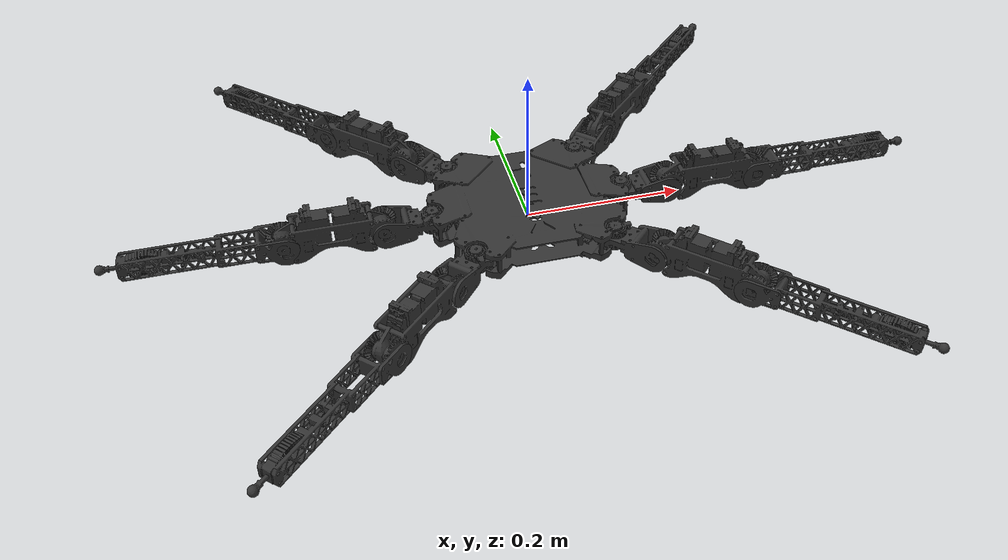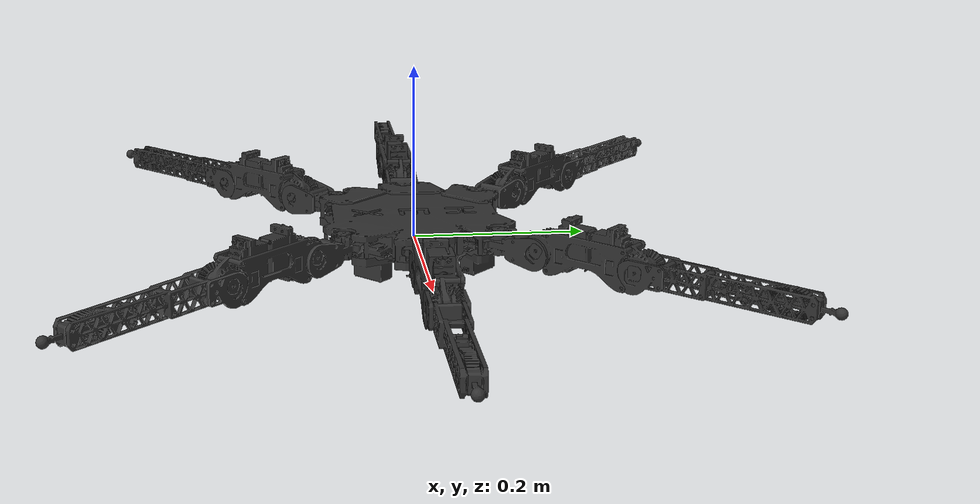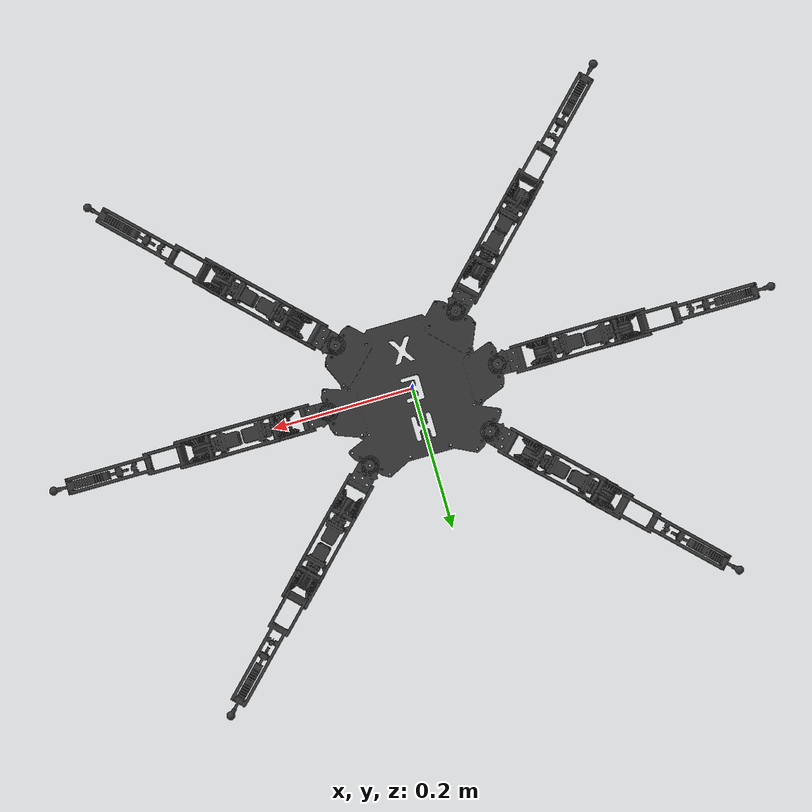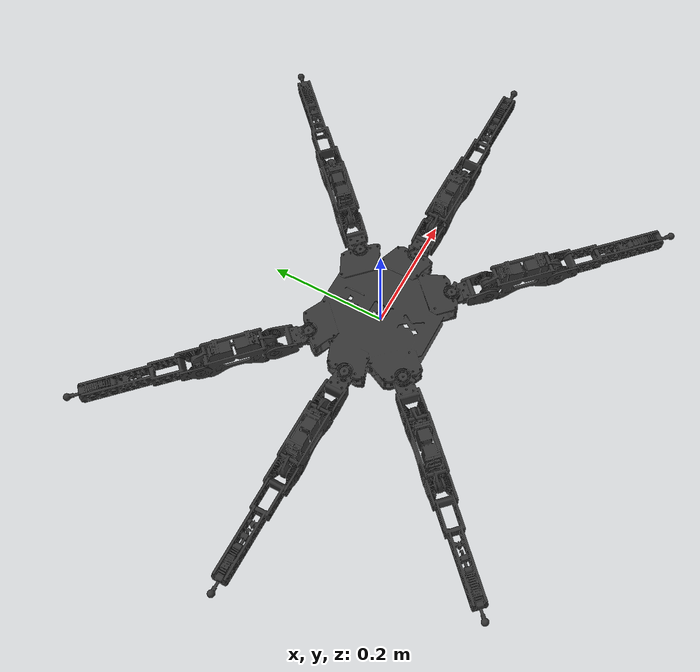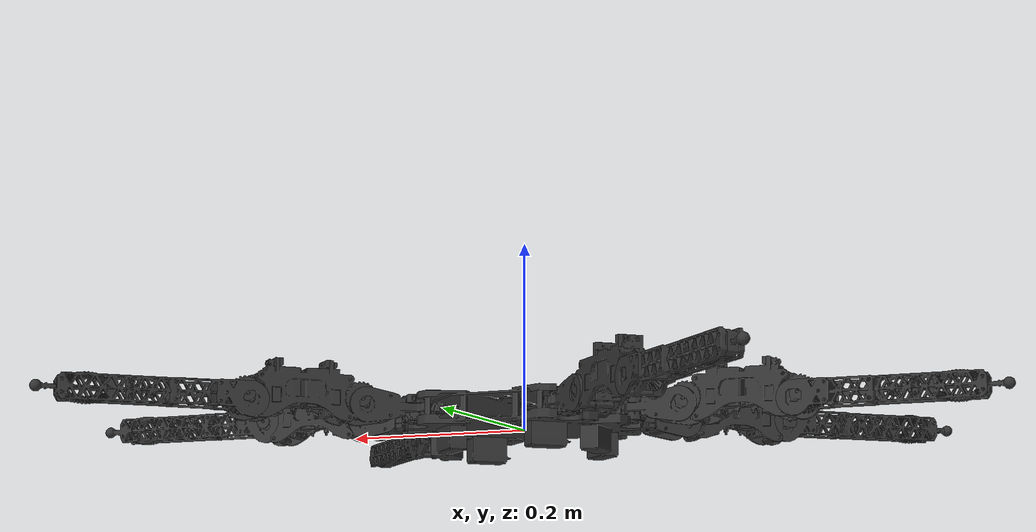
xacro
<?xml version="1.0"?>
<robot name="hexapod" xmlns:xacro="http://ros.org/wiki/xacro">
    <!-- MoveIt configuration for real hardware interface -->
    <!-- This file is optimized for physical robot control -->
    <!-- Used by demo.launch.py when hardware mode is selected -->
    <!-- Default fake_hardware=true allows safe MoveIt testing without real robot -->

    <!-- Robot naming and identification -->
    <xacro:arg name="prefix" default="" />

    <!-- Hardware interface selection for real robot -->
    <xacro:arg name="use_gazebo" default="false" />
    <!-- Default to fake hardware for safe MoveIt algorithm testing -->
    <xacro:arg name="use_fake_hardware" default="true" />
    <xacro:arg name="fake_sensor_commands" default="false" />

    <!-- ESP32 communication parameters for real hardware deployment -->
    <xacro:arg name="port_name" default="/dev/ttyUSB0" />
    <xacro:arg name="baud_rate" default="115200" />

    <!-- Include main hexapod definition from description package -->
    <xacro:include filename="$(find hexapod_description)/urdf/hexapod_ee.urdf.xacro" />

    <!-- Create hexapod robot for MoveIt hardware interface -->
    <xacro:hexapod_ee
        use_sim="true"
        prefix="$(arg prefix)"
        use_gazebo="$(arg use_gazebo)"
        use_fake_hardware="$(arg use_fake_hardware)"
        fake_sensor_commands="$(arg fake_sensor_commands)"
        port_name="$(arg port_name)"
        baud_rate="$(arg baud_rate)" />
</robot>

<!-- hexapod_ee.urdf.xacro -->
<robot name="hexapod" xmlns:xacro="http://ros.org/wiki/xacro">
  <xacro:macro name="hexapod_ee" params="use_sim prefix use_gazebo use_fake_hardware fake_sensor_commands port_name baud_rate">

    <!-- COMPONENT INCLUDES                                                -->
    <!-- Gazebo physics -->
    <xacro:include filename="$(find hexapod_description)/gazebo/hexapod.gazebo.xacro" />

    <!-- Robot structural components (legs, platform, joints) -->
    <xacro:include filename="$(find hexapod_description)/urdf/hexapod_leg_ee.urdf.xacro" />

    <!-- IMU sensor definition (currently unused) -->
    <xacro:include filename="$(find hexapod_description)/urdf/imu.urdf.xacro"/>

    <!-- ros2_control hardware interface configuration -->
    <xacro:include filename="$(find hexapod_description)/control/hexapod.ros2_control.xacro" />

    <!-- ROBOT STRUCTURE INSTANTIATION                                     -->
    <!-- Create complete robot structure with legs and platform -->
    <xacro:hexapod_leg_ee prefix="${prefix}"/>

    <!-- Apply Gazebo physics properties and transmissions -->
    <xacro:hexapod_gazebo prefix="${prefix}" />

    <!-- IMU sensor instantiation (commented out - not currently used) -->

    <!-- GAZEBO SIMULATION PLUGINS                                         -->
    <!-- ros2_control integration plugin for Gazebo -->
    <gazebo>
      <plugin filename="gz_ros2_control-system" name="gz_ros2_control::GazeboSimROS2ControlPlugin">
        <parameters>$(find hexapod_description)/control/controller_manager.yaml</parameters>
      </plugin>
    </gazebo>

    <!-- Touch/contact detection plugin for ground interaction -->
    <gazebo>
      <plugin filename="gz-sim-touchplugin-system"
        name="gz::sim::systems::TouchPlugin">
          <target>ground_plane</target>
          <namespace>tip</namespace>
          <time>0.001</time>
          <enabled>true</enabled>
      </plugin>
    </gazebo>

    <!-- Direct IMU sensor on base platform (alternative to macro) -->
    <gazebo reference="${prefix}base_link">
      <sensor name="imu_sensor" type="imu">
        <update_rate>1</update_rate>
        <always_on>true</always_on>
        <visualize>false</visualize>
        <topic>imu</topic>
      </sensor>
    </gazebo>

    <!-- CONTROL SYSTEM CONFIGURATION                                      -->
    <!-- ros2_control hardware interface with parameter selection -->
    <xacro:hexapod_ros2_control
        name="hexapod"
        initial_positions_file="$(find hexapod_description)/config/initial_positions.yaml"
        use_gazebo="${use_gazebo}"
        use_fake_hardware="${use_fake_hardware}"
        fake_sensor_commands="${fake_sensor_commands}"
        port_name="${port_name}"
        baud_rate="${baud_rate}" />
  </xacro:macro>
</robot>

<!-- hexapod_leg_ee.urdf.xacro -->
<robot xmlns:xacro="http://www.ros.org/wiki/xacro">
  <xacro:macro name="hexapod_leg_ee" params="prefix">

    <!-- PHYSICAL PROPERTIES AND CONSTRAINTS       -->

    <!-- Mass properties for each component -->
    <xacro:property name="platform_mass" value="0.8095" />
    <xacro:property name="up_section_mass" value="0.059" />
    <xacro:property name="mid_section_mass" value="0.1705" />
    <xacro:property name="down_section_mass" value="0.090" />
    <xacro:property name="tip_mass" value="0.001"/>

    <!-- Joint angle limits (radians) -->
    <xacro:property name="joint1_lower" value="-0.785398163"/>
    <xacro:property name="joint1_upper" value="0.785398163"/>
    <xacro:property name="joint2_lower" value="-1.047197551"/>
    <xacro:property name="joint2_upper" value="1.047197551"/>
    <xacro:property name="joint3_lower" value="-0.523598776"/>  <!-- -30° to 90° -->
    <xacro:property name="joint3_upper" value="1.570796327"/>

    <!-- Servo motor specifications -->
    <xacro:property name="joint1_effort" value="2.548"/>      <!-- Nm -->
    <xacro:property name="joint2_effort" value="1.911"/>
    <xacro:property name="joint3_effort" value="1.911"/>

    <xacro:property name="joint1_velocity" value="3.1"/>      <!-- rad/s -->
    <xacro:property name="joint2_velocity" value="4.1"/>
    <xacro:property name="joint3_velocity" value="4.1"/>

    <!-- Platform inertial properties -->
    <xacro:property name="platform_ixx" value="2.782630e-03"/>
    <xacro:property name="platform_ixy" value="3.151174e-07"/>
    <xacro:property name="platform_ixz" value="-3.746570e-07"/>
    <xacro:property name="platform_iyy" value="3.491645e-03"/>
    <xacro:property name="platform_iyz" value="8.425825e-06"/>
    <xacro:property name="platform_izz" value="5.824094e-03"/>

    <!-- End effector inertial properties -->
    <xacro:property name="tip_ixx" value="0.0000000144"/>
    <xacro:property name="tip_iyy" value="0.0000000144"/>
    <xacro:property name="tip_izz" value="0.0000000144"/>
    <xacro:property name="tip_ixy" value="0.0"/>
    <xacro:property name="tip_ixz" value="0.0"/>
    <xacro:property name="tip_iyz" value="0.0"/>

    <!-- LEG 1 - FRONT RIGHT                       -->

    <!-- Joint positions and orientations -->
    <xacro:property name="joint1_1_xyz" value="0.086185	0.0860902	0.0170504"/>
    <xacro:property name="joint1_1_axis" value="0	0	1"/>
    <xacro:property name="joint2_1_xyz" value="0.041059	0.0410588	0.0002496"/>
    <xacro:property name="joint2_1_axis" value="-0.707106781	0.707106781	0"/>
    <xacro:property name="joint3_1_xyz" value="0.085418	0.085419	0"/>
    <xacro:property name="joint3_1_axis" value="-0.707106781	0.707106781	0"/>
    <xacro:property name="joint4_1_xyz" value="0.150968	0.151062	0.004855"/>
    <xacro:property name="joint4_1_axis" value="0	0	0"/>

    <!-- Link visual origins and orientations -->
    <xacro:property name="link2_1_xyz" value="0.0136626	0.0135428	0.0000671"/>
    <xacro:property name="link2_1_rpy" value="0	0	0.7853981634"/>
    <xacro:property name="link3_1_xyz" value="0.04295	0.042401	0.0055591"/>
    <xacro:property name="link3_1_rpy" value="0	0	0.7853981634"/>
    <xacro:property name="link4_1_xyz" value="0.068436	0.068583	0.0042679"/>
    <xacro:property name="link4_1_rpy" value="0	0	0.7853981634"/>
    <xacro:property name="link5_1_xyz" value="0	0	0"/>
    <xacro:property name="link_tip_1_rpy" value="0 0 0.785398163"/>

    <!-- Inertial properties for leg 1 links -->
    <xacro:property name="upper_leg_1_ixx" value="3.192059e-05"/>
    <xacro:property name="upper_leg_1_ixy" value="-1.816964e-05"/>
    <xacro:property name="upper_leg_1_ixz" value="-1.971549e-07"/>
    <xacro:property name="upper_leg_1_iyy" value="3.172578e-05"/>
    <xacro:property name="upper_leg_1_iyz" value="-6.665934e-08"/>
    <xacro:property name="upper_leg_1_izz" value="5.413813e-05"/>

    <xacro:property name="mid_leg_1_ixx" value="1.872470e-04"/>
    <xacro:property name="mid_leg_1_ixy" value="-1.227141e-04"/>
    <xacro:property name="mid_leg_1_ixz" value="4.021989e-08"/>
    <xacro:property name="mid_leg_1_iyy" value="1.872811e-04"/>
    <xacro:property name="mid_leg_1_iyz" value="7.655518e-08"/>
    <xacro:property name="mid_leg_1_izz" value="2.854110e-04"/>

    <xacro:property name="lower_leg_1_ixx" value="1.914881e-04"/>
    <xacro:property name="lower_leg_1_ixy" value="-1.742340e-04"/>
    <xacro:property name="lower_leg_1_ixz" value="-8.359193e-06"/>
    <xacro:property name="lower_leg_1_iyy" value="1.914337e-04"/>
    <xacro:property name="lower_leg_1_iyz" value="-8.346770e-06"/>
    <xacro:property name="lower_leg_1_izz" value="3.656178e-04"/>

    <!-- LEG 2 - FRONT MIDDLE                      -->

    <xacro:property name="joint1_2_xyz" value="0.121845	0	0.0170504"/>
    <xacro:property name="joint1_2_axis" value="0	0	1"/>
    <xacro:property name="joint2_2_xyz" value="0.058105	-0.000094711	0.0002496"/>
    <xacro:property name="joint2_2_axis" value="0	1	0"/>
    <xacro:property name="joint3_2_xyz" value="0.120802	0.000000002	0"/>
    <xacro:property name="joint3_2_axis" value="0	1	0"/>
    <xacro:property name="joint4_2_xyz" value="0.213498	-0.000094709	0.004855"/>
    <xacro:property name="joint4_2_axis" value="0	0	0"/>

    <xacro:property name="link2_2_xyz" value="0.01929	0	0.0001208"/>
    <xacro:property name="link2_2_rpy" value="0	0	0"/>
    <xacro:property name="link3_2_xyz" value="0.060281	0.000094711	0.0055591"/>
    <xacro:property name="link3_2_rpy" value="0	0	0"/>
    <xacro:property name="link4_2_xyz" value="0.096777	0.000131643	0.0042688"/>
    <xacro:property name="link4_2_rpy" value="0	0	0"/>
    <xacro:property name="link5_2_xyz" value="0	0	0"/>
    <xacro:property name="link5_2_rpy" value="0	0	0"/>
    <xacro:property name="link_tip_2_rpy" value="0 0 0"/>

    <xacro:property name="upper_leg_2_ixx" value="1.365355e-05"/>
    <xacro:property name="upper_leg_2_ixy" value="-9.739604e-08"/>
    <xacro:property name="upper_leg_2_ixz" value="-1.865458e-07"/>
    <xacro:property name="upper_leg_2_iyy" value="4.999283e-05"/>
    <xacro:property name="upper_leg_2_iyz" value="9.227452e-08"/>
    <xacro:property name="upper_leg_2_izz" value="5.413814e-05"/>

    <xacro:property name="mid_leg_2_ixx" value="6.454984e-05"/>
    <xacro:property name="mid_leg_2_ixy" value="1.704929e-08"/>
    <xacro:property name="mid_leg_2_ixz" value="8.257522e-08"/>
    <xacro:property name="mid_leg_2_iyy" value="3.099780e-04"/>
    <xacro:property name="mid_leg_2_iyz" value="2.569509e-08"/>
    <xacro:property name="mid_leg_2_izz" value="2.854109e-04"/>

    <xacro:property name="lower_leg_2_ixx" value="1.722692e-05"/>
    <xacro:property name="lower_leg_2_ixy" value="-2.723387e-08"/>
    <xacro:property name="lower_leg_2_ixz" value="-1.181289e-05"/>
    <xacro:property name="lower_leg_2_iyy" value="3.656948e-04"/>
    <xacro:property name="lower_leg_2_iyz" value="8.783736e-09"/>
    <xacro:property name="lower_leg_2_izz" value="3.656178e-04"/>

    <!-- LEG 3 - FRONT LEFT                        -->

    <xacro:property name="joint1_3_xyz" value="0.0861847	-0.0860902	0.0170504"/>
    <xacro:property name="joint1_3_axis" value="0	0	1"/>
    <xacro:property name="joint2_3_xyz" value="0.0410583	-0.0412488	0.0002496"/>
    <xacro:property name="joint2_3_axis" value="0.707106781	0.707106781	0"/>
    <xacro:property name="joint3_3_xyz" value="0.08542	-0.085418	0"/>
    <xacro:property name="joint3_3_axis" value="0.707106781	0.707106781	0"/>
    <xacro:property name="joint4_3_xyz" value="0.150967	-0.150873	0.004855"/>
    <xacro:property name="joint4_3_axis" value="0	0	0"/>

    <xacro:property name="link2_3_xyz" value="0.0136629	-0.0135428	0.0000671"/>
    <xacro:property name="link2_3_rpy" value="0	0	5.497787144"/>
    <xacro:property name="link3_3_xyz" value="0.042951	-0.042211	0.0055591"/>
    <xacro:property name="link3_3_rpy" value="0	0	5.497787144"/>
    <xacro:property name="link4_3_xyz" value="0.068435	-0.068394	0.0042679"/>
    <xacro:property name="link4_3_rpy" value="0	0	5.497787144"/>
    <xacro:property name="link5_3_xyz" value="0	0	0"/>
    <xacro:property name="link5_3_rpy" value="0	0	0"/>
    <xacro:property name="link_tip_3_rpy" value="0 0 5.497787144"/>

    <xacro:property name="upper_leg_3_ixx" value="3.172580e-05"/>
    <xacro:property name="upper_leg_3_ixy" value="1.816965e-05"/>
    <xacro:property name="upper_leg_3_ixz" value="-6.666029e-08"/>
    <xacro:property name="upper_leg_3_iyy" value="3.192058e-05"/>
    <xacro:property name="upper_leg_3_iyz" value="1.971555e-07"/>
    <xacro:property name="upper_leg_3_izz" value="5.413814e-05"/>

    <xacro:property name="mid_leg_3_ixx" value="1.872811e-04"/>
    <xacro:property name="mid_leg_3_ixy" value="1.227142e-04"/>
    <xacro:property name="mid_leg_3_ixz" value="7.655505e-08"/>
    <xacro:property name="mid_leg_3_iyy" value="1.872470e-04"/>
    <xacro:property name="mid_leg_3_iyz" value="-4.021846e-08"/>
    <xacro:property name="mid_leg_3_izz" value="2.854111e-04"/>

    <xacro:property name="lower_leg_3_ixx" value="1.914336e-04"/>
    <xacro:property name="lower_leg_3_ixy" value="1.742339e-04"/>
    <xacro:property name="lower_leg_3_ixz" value="-8.346764e-06"/>
    <xacro:property name="lower_leg_3_iyy" value="1.914880e-04"/>
    <xacro:property name="lower_leg_3_iyz" value="8.359190e-06"/>
    <xacro:property name="lower_leg_3_izz" value="3.656177e-04"/>

    <!-- LEG 4 - REAR LEFT                         -->

    <xacro:property name="joint1_4_xyz" value="-0.0861847	-0.0860902	0.0170504"/>
    <xacro:property name="joint1_4_axis" value="0	0	1"/>
    <xacro:property name="joint2_4_xyz" value="-0.0410583	-0.0412488	0.0002496"/>
    <xacro:property name="joint2_4_axis" value="0.707106781	-0.707106781	0"/>
    <xacro:property name="joint3_4_xyz" value="-0.08542	-0.085418	0"/>
    <xacro:property name="joint3_4_axis" value="0.707106781	-0.707106781	0"/>
    <xacro:property name="joint4_4_xyz" value="-0.150967	-0.150873	0.004855"/>
    <xacro:property name="joint4_4_axis" value="0	0	0"/>

    <xacro:property name="link2_4_xyz" value="-0.0136629	-0.0135428	0.0000671"/>
    <xacro:property name="link2_4_rpy" value="0	0	3.926990817"/>
    <xacro:property name="link3_4_xyz" value="-0.042951	-0.042211	0.0055591"/>
    <xacro:property name="link3_4_rpy" value="0	0	3.926990817"/>
    <xacro:property name="link4_4_xyz" value="-0.068435	-0.068394	0.0042679"/>
    <xacro:property name="link4_4_rpy" value="0	0	3.926990817"/>
    <xacro:property name="link5_4_xyz" value="0	0	0"/>
    <xacro:property name="link5_4_rpy" value="0	0	0"/>
    <xacro:property name="link_tip_4_rpy" value="0 0 3.926990817"/>

    <xacro:property name="upper_leg_4_ixx" value="3.192057e-05"/>
    <xacro:property name="upper_leg_4_ixy" value="-1.816963e-05"/>
    <xacro:property name="upper_leg_4_ixz" value="1.971549e-07"/>
    <xacro:property name="upper_leg_4_iyy" value="3.172578e-05"/>
    <xacro:property name="upper_leg_4_iyz" value="6.665899e-08"/>
    <xacro:property name="upper_leg_4_izz" value="5.413811e-05"/>

    <xacro:property name="mid_leg_4_ixx" value="1.872469e-04"/>
    <xacro:property name="mid_leg_4_ixy" value="-1.227141e-04"/>
    <xacro:property name="mid_leg_4_ixz" value="-4.021828e-08"/>
    <xacro:property name="mid_leg_4_iyy" value="1.872811e-04"/>
    <xacro:property name="mid_leg_4_iyz" value="-7.655551e-08"/>
    <xacro:property name="mid_leg_4_izz" value="2.854110e-04"/>

    <xacro:property name="lower_leg_4_ixx" value="1.914881e-04"/>
    <xacro:property name="lower_leg_4_ixy" value="-1.742340e-04"/>
    <xacro:property name="lower_leg_4_ixz" value="8.359195e-06"/>
    <xacro:property name="lower_leg_4_iyy" value="1.914337e-04"/>
    <xacro:property name="lower_leg_4_iyz" value="8.346770e-06"/>
    <xacro:property name="lower_leg_4_izz" value="3.656178e-04"/>

    <!-- LEG 5 - REAR MIDDLE                       -->

    <xacro:property name="joint1_5_xyz" value="-0.121845	0	0.0170504"/>
    <xacro:property name="joint1_5_axis" value="0	0	1"/>
    <xacro:property name="joint2_5_xyz" value="-0.058105	-0.000094711	0.0002496"/>
    <xacro:property name="joint2_5_axis" value="0	-1	0"/>
    <xacro:property name="joint3_5_xyz" value="-0.120802	0.000000002	0"/>
    <xacro:property name="joint3_5_axis" value="0	-1	0"/>
    <xacro:property name="joint4_5_xyz" value="-0.213498	0.000094709	0.004855"/>
    <xacro:property name="joint4_5_axis" value="0	0	0"/>

    <xacro:property name="link2_5_xyz" value="-0.01929	0	0.0001208"/>
    <xacro:property name="link2_5_rpy" value="0	0	3.141592654"/>
    <xacro:property name="link3_5_xyz" value="-0.060281	0.000094711	0.0055591"/>
    <xacro:property name="link3_5_rpy" value="0	0	3.141592654"/>
    <xacro:property name="link4_5_xyz" value="-0.096777	0.000131643	0.0042688"/>
    <xacro:property name="link4_5_rpy" value="0	0	3.141592654"/>
    <xacro:property name="link5_5_xyz" value="0	0	0"/>
    <xacro:property name="link5_5_rpy" value="0	0	0"/>
    <xacro:property name="link_tip_5_rpy" value="0 0 3.141592654"/>

    <xacro:property name="upper_leg_5_ixx" value="1.365355e-05"/>
    <xacro:property name="upper_leg_5_ixy" value="-9.739963e-08"/>
    <xacro:property name="upper_leg_5_ixz" value="1.865460e-07"/>
    <xacro:property name="upper_leg_5_iyy" value="4.999284e-05"/>
    <xacro:property name="upper_leg_5_iyz" value="-9.227461e-08"/>
    <xacro:property name="upper_leg_5_izz" value="5.413814e-05"/>

    <xacro:property name="mid_leg_5_ixx" value="6.454984e-05"/>
    <xacro:property name="mid_leg_5_ixy" value="1.702660e-08"/>
    <xacro:property name="mid_leg_5_ixz" value="-8.257650e-08"/>
    <xacro:property name="mid_leg_5_iyy" value="3.099780e-04"/>
    <xacro:property name="mid_leg_5_iyz" value="-2.569593e-08"/>
    <xacro:property name="mid_leg_5_izz" value="2.854108e-04"/>

    <xacro:property name="lower_leg_5_ixx" value="1.722692e-05"/>
    <xacro:property name="lower_leg_5_ixy" value="-2.726535e-08"/>
    <xacro:property name="lower_leg_5_ixz" value="1.181289e-05"/>
    <xacro:property name="lower_leg_5_iyy" value="3.656948e-04"/>
    <xacro:property name="lower_leg_5_iyz" value="-8.782921e-09"/>
    <xacro:property name="lower_leg_5_izz" value="3.656178e-04"/>

    <!-- LEG 6 - REAR RIGHT                        -->

    <xacro:property name="joint1_6_xyz" value="-0.0859957	0.0860903	0.0170505"/>
    <xacro:property name="joint1_6_axis" value="0	0	1"/>
    <xacro:property name="joint2_6_xyz" value="-0.0412483	0.0410587	0.0002494"/>
    <xacro:property name="joint2_6_axis" value="-0.707106781	-0.707106781	0"/>
    <xacro:property name="joint3_6_xyz" value="-0.08542	0.085419	0.0000001"/>
    <xacro:property name="joint3_6_axis" value="-0.707106781	-0.707106781	0"/>
    <xacro:property name="joint4_6_xyz" value="-0.150966	0.151062	0.004855"/>
    <xacro:property name="joint4_6_axis" value="0	0	0"/>

    <xacro:property name="link2_6_xyz" value="-0.0138519	0.0135427	0.000067"/>
    <xacro:property name="link2_6_rpy" value="0	0	2.35619449"/>
    <xacro:property name="link3_6_xyz" value="-0.04295	0.042401	0.0055592"/>
    <xacro:property name="link3_6_rpy" value="0	0	2.364921136"/>
    <xacro:property name="link4_6_xyz" value="-0.068434	0.068583	0.0042679"/>
    <xacro:property name="link4_6_rpy" value="0	0	2.35619449"/>
    <xacro:property name="link5_6_xyz" value="0	0	0"/>
    <xacro:property name="link5_6_rpy" value="0	0	0"/>
    <xacro:property name="link_tip_6_rpy" value="0 0 2.35619449"/>

    <xacro:property name="upper_leg_6_ixx" value="3.172579e-05"/>
    <xacro:property name="upper_leg_6_ixy" value="1.816965e-05"/>
    <xacro:property name="upper_leg_6_ixz" value="6.665998e-08"/>
    <xacro:property name="upper_leg_6_iyy" value="3.192060e-05"/>
    <xacro:property name="upper_leg_6_iyz" value="-1.971554e-07"/>
    <xacro:property name="upper_leg_6_izz" value="5.413815e-05"/>

    <xacro:property name="mid_leg_6_ixx" value="1.872811e-04"/>
    <xacro:property name="mid_leg_6_ixy" value="1.227142e-04"/>
    <xacro:property name="mid_leg_6_ixz" value="-7.655812e-08"/>
    <xacro:property name="mid_leg_6_iyy" value="1.872470e-04"/>
    <xacro:property name="mid_leg_6_iyz" value="4.021840e-08"/>
    <xacro:property name="mid_leg_6_izz" value="2.854111e-04"/>

    <xacro:property name="lower_leg_6_ixx" value="1.914336e-04"/>
    <xacro:property name="lower_leg_6_ixy" value="1.742339e-04"/>
    <xacro:property name="lower_leg_6_ixz" value="8.346770e-06"/>
    <xacro:property name="lower_leg_6_iyy" value="1.914881e-04"/>
    <xacro:property name="lower_leg_6_iyz" value="-8.359189e-06"/>
    <xacro:property name="lower_leg_6_izz" value="3.656177e-04"/>

    <!-- MESH AND COLLISION MODEL SETUP            -->

    <!-- Path to 3D mesh files -->
    <xacro:property
        name="meshes_file_direction"
        value="package://hexapod_description/meshes/Version2"/>

    <!-- Include collision model definitions -->
    <xacro:include filename="$(find hexapod_description)/collision/Version2/platform_hitbox.xacro"/>
    <xacro:include filename="$(find hexapod_description)/collision/Version2/up_section_hitbox.xacro"/>
    <xacro:include filename="$(find hexapod_description)/collision/Version2/mid_section_hitbox.xacro"/>
    <xacro:include filename="$(find hexapod_description)/collision/Version2/down_section_hitbox.xacro"/>
    <xacro:include filename="$(find hexapod_description)/collision/Version2/tip_hitbox.xacro"/>

    <!-- MACRO DEFINITIONS                          -->

    <!-- Platform/Base macro -->
    <xacro:macro name="platform_base" params="prefix ixx ixy ixz iyy iyz izz">
      <link name="${prefix}base_link">
        <visual>
          <origin xyz="0.00001	0.003706	0.007688" rpy="0 0 0"/>
          <geometry>
            <mesh filename="${meshes_file_direction}/platform.stl" scale="1 1 1"/>
          </geometry>
          <material name="gray">
            <color rgba="0.2 0.2 0.2 1"/>
          </material>
        </visual>

        <!-- Collision model using simplified shapes -->
        <xacro:platform_collision prefix="${prefix}" />
        <inertial>
          <origin xyz="0.00001	0.003706	0.007688" rpy="0 0 0"/>
          <mass value="${platform_mass}"/>
          <inertia
            ixx="${ixx}" ixy="${ixy}" ixz="${ixz}"
            iyy="${iyy}" iyz="${iyz}"
            izz="${izz}"/>
        </inertial>
      </link>
    </xacro:macro>

    <!-- Joint macro -->
    <xacro:macro name="leg_joint" params="prefix joint_name parent_link child_link xyz axis lower upper effort velocity">
      <joint name="${joint_name}" type="revolute">
        <parent link="${parent_link}"/>
        <child link="${child_link}"/>
        <origin xyz="${xyz}" rpy="0 0 0"/>
        <axis xyz="${axis}"/>
        <limit effort="${effort}" velocity="${velocity}" lower="${lower}" upper="${upper}"/>
        <dynamics damping="0.1"/>
      </joint>
    </xacro:macro>

    <!-- Upper leg segment macro -->
    <xacro:macro name="upper_leg" params="prefix index xyz rpy ixx ixy ixz iyy iyz izz">
      <link name="${prefix}link2_${index}">
        <visual>
          <origin xyz="${xyz}" rpy="${rpy}"/>
          <geometry>
            <mesh filename="${meshes_file_direction}/leg_up.stl" scale="1.0 1.0 1.0"/>
          </geometry>
          <material name="grey">
            <color rgba="0.2 0.2 0.2 1"/>
          </material>
        </visual>

        <!-- Collision model -->
        <xacro:upper_leg_collision prefix="${prefix}" position="${xyz}" rotation="${rpy}"/>
        <inertial>
          <origin xyz="${xyz}" rpy="0.0 0.0 0.0"/>
          <mass value="${up_section_mass}"/>
          <inertia ixx="${ixx}" ixy="${ixy}" ixz="${ixz}" iyy="${iyy}" iyz="${iyz}" izz="${izz}"/>
        </inertial>
      </link>
    </xacro:macro>

    <!-- Middle leg segment macro -->
    <xacro:macro name="mid_leg" params="prefix index xyz rpy ixx ixy ixz iyy iyz izz">
      <link name="${prefix}link3_${index}">
        <visual>
          <origin xyz="${xyz}" rpy="${rpy}"/>
          <geometry>
            <mesh filename="${meshes_file_direction}/leg_mid.stl" scale="1.0 1.0 1.0"/>
          </geometry>
          <material name="grey">
            <color rgba="0.2 0.2 0.2 1"/>
          </material>
        </visual>
        <xacro:mid_leg_collision prefix="${prefix}" position="${xyz}" rotation="${rpy}"/>
        <inertial>
          <origin xyz="${xyz}" rpy="${rpy}"/>
          <mass value="${mid_section_mass}"/>
          <inertia ixx="${ixx}" ixy="${ixy}" ixz="${ixz}" iyy="${iyy}" iyz="${iyz}" izz="${izz}"/>
        </inertial>
      </link>
    </xacro:macro>

    <!-- Lower leg segment macro -->
    <xacro:macro name="lower_leg" params="prefix index xyz rpy ixx ixy ixz iyy iyz izz">
      <link name="${prefix}link4_${index}">
        <visual>
          <origin xyz="${xyz}" rpy="${rpy}"/>
          <geometry>
            <mesh filename="${meshes_file_direction}/leg_down.stl" scale="1.0 1.0 1.0"/>
          </geometry>
          <material name="grey">
            <color rgba="0.2 0.2 0.2 1"/>
          </material>
        </visual>
        <xacro:lower_leg_collision prefix="${prefix}" position="${xyz}" rotation="${rpy}"/>
        <inertial>
          <origin xyz="${xyz}" rpy="${rpy}"/>
          <mass value="${down_section_mass}"/>
          <inertia ixx="${ixx}" ixy="${ixy}" ixz="${ixz}" iyy="${iyy}" iyz="${iyz}" izz="${izz}"/>
        </inertial>
      </link>
    </xacro:macro>

    <!-- End effector joint macro -->
    <xacro:macro name="end_effector_joint" params="prefix index xyz rpy">
      <joint name="${prefix}joint4_${index}" type="fixed">
        <parent link="${prefix}link4_${index}"/>
        <child link="${prefix}link5_${index}"/>
        <origin xyz="${xyz}" rpy="${rpy}"/>
      </joint>
    </xacro:macro>

    <!-- End effector link macro -->
    <xacro:macro name="end_effector_link" params="prefix index rpy">
      <link name="${prefix}link5_${index}">
        <xacro:tip_collision prefix="${prefix}" rotation="${rpy}"/>
        <inertial>
        <origin xyz="0 0 0" rpy="0 0 0"/>
        <mass value="${tip_mass}"/>
        <inertia
          ixx="${tip_ixx}" ixy="${tip_ixy}" ixz="${tip_ixz}"
          iyy="${tip_iyy}" iyz="${tip_iyz}"
          izz="${tip_izz}"/>
      </inertial>
      <visual>
        <origin xyz="0 0 0" rpy="0 0 0"/>
        <geometry>
          <sphere radius="0.005"/>
        </geometry>
        <material name="grey">
          <color rgba="0.2 0.2 0.2 1"/>
        </material>
      </visual>
      </link>
    </xacro:macro>

    <!-- MAIN HEXAPOD ASSEMBLY                     -->

    <xacro:macro name="hexapod" params="prefix">
        <!-- Create base platform -->
      <xacro:platform_base
        prefix="${prefix}"
        ixx="${platform_ixx}"
        ixy="${platform_ixy}"
        ixz="${platform_ixz}"
        iyy="${platform_iyy}"
        iyz="${platform_iyz}"
        izz="${platform_izz}"/>

      <!-- LEG 1 Assembly -->
      <xacro:leg_joint
        prefix="${prefix}"
        joint_name="${prefix}joint1_1"
        parent_link="${prefix}base_link"
        child_link="${prefix}link2_1"
        xyz="${joint1_1_xyz}"
        axis="${joint1_1_axis}"
        lower="${joint1_lower}"
        upper="${joint1_upper}"
        effort="${joint1_effort}"
        velocity="${joint1_velocity}"/>
      <xacro:upper_leg
        prefix="${prefix}"
        index="1"
        xyz="${link2_1_xyz}"
        rpy="${link2_1_rpy}"
        ixx="${upper_leg_1_ixx}"
        ixy="${upper_leg_1_ixy}"
        ixz="${upper_leg_1_ixz}"
        iyy="${upper_leg_1_iyy}"
        iyz="${upper_leg_1_iyz}"
        izz="${upper_leg_1_izz}"/>

      <xacro:leg_joint
        prefix="${prefix}"
        joint_name="${prefix}joint2_1"
        parent_link="${prefix}link2_1"
        child_link="${prefix}link3_1"
        xyz="${joint2_1_xyz}"
        axis="${joint2_1_axis}"
        lower="${joint2_lower}"
        upper="${joint2_upper}"
        effort="${joint2_effort}"
        velocity="${joint2_velocity}"/>
      <xacro:mid_leg
        prefix="${prefix}"
        index="1"
        xyz="${link3_1_xyz}"
        rpy="${link3_1_rpy}"
        ixx="${mid_leg_1_ixx}"
        ixy="${mid_leg_1_ixy}"
        ixz="${mid_leg_1_ixz}"
        iyy="${mid_leg_1_iyy}"
        iyz="${mid_leg_1_iyz}"
        izz="${mid_leg_1_izz}"/>

      <xacro:leg_joint
        prefix="${prefix}"
        joint_name="${prefix}joint3_1"
        parent_link="${prefix}link3_1"
        child_link="${prefix}link4_1"
        xyz="${joint3_1_xyz}"
        axis="${joint3_1_axis}"
        lower="${joint3_lower}"
        upper="${joint3_upper}"
        effort="${joint3_effort}"
        velocity="${joint3_velocity}"/>
      <xacro:lower_leg
        prefix="${prefix}"
        index="1"
        xyz="${link4_1_xyz}"
        rpy="${link4_1_rpy}"
        ixx="${lower_leg_1_ixx}"
        ixy="${lower_leg_1_ixy}"
        ixz="${lower_leg_1_ixz}"
        iyy="${lower_leg_1_iyy}"
        iyz="${lower_leg_1_iyz}"
        izz="${lower_leg_1_izz}"/>

      <xacro:end_effector_joint prefix="${prefix}" index="1" xyz="${joint4_1_xyz}" rpy="${joint4_1_axis}"/>
      <xacro:end_effector_link prefix="${prefix}" index="1" rpy="${link_tip_1_rpy}"/>

      <!-- LEG 2 Assembly -->
      <xacro:leg_joint
        prefix="${prefix}"
        joint_name="${prefix}joint1_2"
        parent_link="${prefix}base_link"
        child_link="${prefix}link2_2"
        xyz="${joint1_2_xyz}"
        axis="${joint1_2_axis}"
        lower="${joint1_lower}"
        upper="${joint1_upper}"
        effort="${joint1_effort}"
        velocity="${joint1_velocity}"/>
      <xacro:upper_leg
        prefix="${prefix}"
        index="2"
        xyz="${link2_2_xyz}"
        rpy="${link2_2_rpy}"
        ixx="${upper_leg_2_ixx}"
        ixy="${upper_leg_2_ixy}"
        ixz="${upper_leg_2_ixz}"
        iyy="${upper_leg_2_iyy}"
        iyz="${upper_leg_2_iyz}"
        izz="${upper_leg_2_izz}"/>

      <xacro:leg_joint
        prefix="${prefix}"
        joint_name="${prefix}joint2_2"
        parent_link="${prefix}link2_2"
        child_link="${prefix}link3_2"
        xyz="${joint2_2_xyz}"
        axis="${joint2_2_axis}"
        lower="${joint2_lower}"
        upper="${joint2_upper}"
        effort="${joint2_effort}"
        velocity="${joint2_velocity}"/>
      <xacro:mid_leg
        prefix="${prefix}"
        index="2"
        xyz="${link3_2_xyz}"
        rpy="${link3_2_rpy}"
        ixx="${mid_leg_2_ixx}"
        ixy="${mid_leg_2_ixy}"
        ixz="${mid_leg_2_ixz}"
        iyy="${mid_leg_2_iyy}"
        iyz="${mid_leg_2_iyz}"
        izz="${mid_leg_2_izz}"/>

      <xacro:leg_joint
        prefix="${prefix}"
        joint_name="${prefix}joint3_2"
        parent_link="${prefix}link3_2"
        child_link="${prefix}link4_2"
        xyz="${joint3_2_xyz}"
        axis="${joint3_2_axis}"
        lower="${joint3_lower}"
        upper="${joint3_upper}"
        effort="${joint3_effort}"
        velocity="${joint3_velocity}"/>
      <xacro:lower_leg
        prefix="${prefix}"
        index="2"
        xyz="${link4_2_xyz}"
        rpy="${link4_2_rpy}"
        ixx="${lower_leg_2_ixx}"
        ixy="${lower_leg_2_ixy}"
        ixz="${lower_leg_2_ixz}"
        iyy="${lower_leg_2_iyy}"
        iyz="${lower_leg_2_iyz}"
        izz="${lower_leg_2_izz}"/>

      <xacro:end_effector_joint prefix="${prefix}" index="2" xyz="${joint4_2_xyz}" rpy="${joint4_2_axis}"/>
      <xacro:end_effector_link prefix="${prefix}" index="2" rpy="${link_tip_2_rpy}"/>

      <!-- LEG 3 Assembly -->
      <xacro:leg_joint
        prefix="${prefix}"
        joint_name="${prefix}joint1_3"
        parent_link="${prefix}base_link"
        child_link="${prefix}link2_3"
        xyz="${joint1_3_xyz}"
        axis="${joint1_3_axis}"
        lower="${joint1_lower}"
        upper="${joint1_upper}"
        effort="${joint1_effort}"
        velocity="${joint1_velocity}"/>
      <xacro:upper_leg
        prefix="${prefix}"
        index="3"
        xyz="${link2_3_xyz}"
        rpy="${link2_3_rpy}"
        ixx="${upper_leg_3_ixx}"
        ixy="${upper_leg_3_ixy}"
        ixz="${upper_leg_3_ixz}"
        iyy="${upper_leg_3_iyy}"
        iyz="${upper_leg_3_iyz}"
        izz="${upper_leg_3_izz}"/>

      <xacro:leg_joint
        prefix="${prefix}"
        joint_name="${prefix}joint2_3"
        parent_link="${prefix}link2_3"
        child_link="${prefix}link3_3"
        xyz="${joint2_3_xyz}"
        axis="${joint2_3_axis}"
        lower="${joint2_lower}"
        upper="${joint2_upper}"
        effort="${joint2_effort}"
        velocity="${joint2_velocity}"/>
      <xacro:mid_leg
        prefix="${prefix}"
        index="3"
        xyz="${link3_3_xyz}"
        rpy="${link3_3_rpy}"
        ixx="${mid_leg_3_ixx}"
        ixy="${mid_leg_3_ixy}"
        ixz="${mid_leg_3_ixz}"
        iyy="${mid_leg_3_iyy}"
        iyz="${mid_leg_3_iyz}"
        izz="${mid_leg_3_izz}"/>

      <xacro:leg_joint
        prefix="${prefix}"
        joint_name="${prefix}joint3_3"
        parent_link="${prefix}link3_3"
        child_link="${prefix}link4_3"
        xyz="${joint3_3_xyz}"
        axis="${joint3_3_axis}"
        lower="${joint3_lower}"
        upper="${joint3_upper}"
        effort="${joint3_effort}"
        velocity="${joint3_velocity}"/>
      <xacro:lower_leg
        prefix="${prefix}"
        index="3"
        xyz="${link4_3_xyz}"
        rpy="${link4_3_rpy}"
        ixx="${lower_leg_3_ixx}"
        ixy="${lower_leg_3_ixy}"
        ixz="${lower_leg_3_ixz}"
        iyy="${lower_leg_3_iyy}"
        iyz="${lower_leg_3_iyz}"
        izz="${lower_leg_3_izz}"/>

      <xacro:end_effector_joint prefix="${prefix}" index="3" xyz="${joint4_3_xyz}" rpy="${joint4_3_axis}"/>
      <xacro:end_effector_link prefix="${prefix}" index="3" rpy="${link_tip_3_rpy}"/>

      <!-- LEG 4 Assembly -->
      <xacro:leg_joint
        prefix="${prefix}"
        joint_name="${prefix}joint1_4"
        parent_link="${prefix}base_link"
        child_link="${prefix}link2_4"
        xyz="${joint1_4_xyz}"
        axis="${joint1_4_axis}"
        lower="${joint1_lower}"
        upper="${joint1_upper}"
        effort="${joint1_effort}"
        velocity="${joint1_velocity}"/>
      <xacro:upper_leg
        prefix="${prefix}"
        index="4"
        xyz="${link2_4_xyz}"
        rpy="${link2_4_rpy}"
        ixx="${upper_leg_4_ixx}"
        ixy="${upper_leg_4_ixy}"
        ixz="${upper_leg_4_ixz}"
        iyy="${upper_leg_4_iyy}"
        iyz="${upper_leg_4_iyz}"
        izz="${upper_leg_4_izz}"/>

      <xacro:leg_joint
        prefix="${prefix}"
        joint_name="${prefix}joint2_4"
        parent_link="${prefix}link2_4"
        child_link="${prefix}link3_4"
        xyz="${joint2_4_xyz}"
        axis="${joint2_4_axis}"
        lower="${joint2_lower}"
        upper="${joint2_upper}"
        effort="${joint2_effort}"
        velocity="${joint2_velocity}"/>
      <xacro:mid_leg
        prefix="${prefix}"
        index="4"
        xyz="${link3_4_xyz}"
        rpy="${link3_4_rpy}"
        ixx="${mid_leg_4_ixx}"
        ixy="${mid_leg_4_ixy}"
        ixz="${mid_leg_4_ixz}"
        iyy="${mid_leg_4_iyy}"
        iyz="${mid_leg_4_iyz}"
        izz="${mid_leg_4_izz}"/>

      <xacro:leg_joint
        prefix="${prefix}"
        joint_name="${prefix}joint3_4"
        parent_link="${prefix}link3_4"
        child_link="${prefix}link4_4"
        xyz="${joint3_4_xyz}"
        axis="${joint3_4_axis}"
        lower="${joint3_lower}"
        upper="${joint3_upper}"
        effort="${joint3_effort}"
        velocity="${joint3_velocity}"/>
      <xacro:lower_leg
        prefix="${prefix}"
        index="4"
        xyz="${link4_4_xyz}"
        rpy="${link4_4_rpy}"
        ixx="${lower_leg_4_ixx}"
        ixy="${lower_leg_4_ixy}"
        ixz="${lower_leg_4_ixz}"
        iyy="${lower_leg_4_iyy}"
        iyz="${lower_leg_4_iyz}"
        izz="${lower_leg_4_izz}"/>

      <xacro:end_effector_joint prefix="${prefix}" index="4" xyz="${joint4_4_xyz}" rpy="${joint4_4_axis}"/>
      <xacro:end_effector_link prefix="${prefix}" index="4" rpy="${link_tip_4_rpy}"/>

      <!-- LEG 5 Assembly -->
      <xacro:leg_joint
        prefix="${prefix}"
        joint_name="${prefix}joint1_5"
        parent_link="${prefix}base_link"
        child_link="${prefix}link2_5"
        xyz="${joint1_5_xyz}"
        axis="${joint1_5_axis}"
        lower="${joint1_lower}"
        upper="${joint1_upper}"
        effort="${joint1_effort}"
        velocity="${joint1_velocity}"/>
      <xacro:upper_leg
        prefix="${prefix}"
        index="5"
        xyz="${link2_5_xyz}"
        rpy="${link2_5_rpy}"
        ixx="${upper_leg_5_ixx}"
        ixy="${upper_leg_5_ixy}"
        ixz="${upper_leg_5_ixz}"
        iyy="${upper_leg_5_iyy}"
        iyz="${upper_leg_5_iyz}"
        izz="${upper_leg_5_izz}"/>

      <xacro:leg_joint
        prefix="${prefix}"
        joint_name="${prefix}joint2_5"
        parent_link="${prefix}link2_5"
        child_link="${prefix}link3_5"
        xyz="${joint2_5_xyz}"
        axis="${joint2_5_axis}"
        lower="${joint2_lower}"
        upper="${joint2_upper}"
        effort="${joint2_effort}"
        velocity="${joint2_velocity}"/>
      <xacro:mid_leg
        prefix="${prefix}"
        index="5"
        xyz="${link3_5_xyz}"
        rpy="${link3_5_rpy}"
        ixx="${mid_leg_5_ixx}"
        ixy="${mid_leg_5_ixy}"
        ixz="${mid_leg_5_ixz}"
        iyy="${mid_leg_5_iyy}"
        iyz="${mid_leg_5_iyz}"
        izz="${mid_leg_5_izz}"/>

      <xacro:leg_joint
        prefix="${prefix}"
        joint_name="${prefix}joint3_5"
        parent_link="${prefix}link3_5"
        child_link="${prefix}link4_5"
        xyz="${joint3_5_xyz}"
        axis="${joint3_5_axis}"
        lower="${joint3_lower}"
        upper="${joint3_upper}"
        effort="${joint3_effort}"
        velocity="${joint3_velocity}"/>
      <xacro:lower_leg
        prefix="${prefix}"
        index="5"
        xyz="${link4_5_xyz}"
        rpy="${link4_5_rpy}"
        ixx="${lower_leg_5_ixx}"
        ixy="${lower_leg_5_ixy}"
        ixz="${lower_leg_5_ixz}"
        iyy="${lower_leg_5_iyy}"
        iyz="${lower_leg_5_iyz}"
        izz="${lower_leg_5_izz}"/>

      <xacro:end_effector_joint prefix="${prefix}" index="5" xyz="${joint4_5_xyz}" rpy="${joint4_5_axis}"/>
      <xacro:end_effector_link prefix="${prefix}" index="5" rpy="${link_tip_5_rpy}"/>

      <!-- LEG 6 Assembly -->
      <xacro:leg_joint
        prefix="${prefix}"
        joint_name="${prefix}joint1_6"
        parent_link="${prefix}base_link"
        child_link="${prefix}link2_6"
        xyz="${joint1_6_xyz}"
        axis="${joint1_6_axis}"
        lower="${joint1_lower}"
        upper="${joint1_upper}"
        effort="${joint1_effort}"
        velocity="${joint1_velocity}"/>
      <xacro:upper_leg
        prefix="${prefix}"
        index="6"
        xyz="${link2_6_xyz}"
        rpy="${link2_6_rpy}"
        ixx="${upper_leg_6_ixx}"
        ixy="${upper_leg_6_ixy}"
        ixz="${upper_leg_6_ixz}"
        iyy="${upper_leg_6_iyy}"
        iyz="${upper_leg_6_iyz}"
        izz="${upper_leg_6_izz}"/>

      <xacro:leg_joint
        prefix="${prefix}"
        joint_name="${prefix}joint2_6"
        parent_link="${prefix}link2_6"
        child_link="${prefix}link3_6"
        xyz="${joint2_6_xyz}"
        axis="${joint2_6_axis}"
        lower="${joint2_lower}"
        upper="${joint2_upper}"
        effort="${joint2_effort}"
        velocity="${joint2_velocity}"/>
      <xacro:mid_leg
        prefix="${prefix}"
        index="6"
        xyz="${link3_6_xyz}"
        rpy="${link3_6_rpy}"
        ixx="${mid_leg_6_ixx}"
        ixy="${mid_leg_6_ixy}"
        ixz="${mid_leg_6_ixz}"
        iyy="${mid_leg_6_iyy}"
        iyz="${mid_leg_6_iyz}"
        izz="${mid_leg_6_izz}"/>

      <xacro:leg_joint
        prefix="${prefix}"
        joint_name="${prefix}joint3_6"
        parent_link="${prefix}link3_6"
        child_link="${prefix}link4_6"
        xyz="${joint3_6_xyz}"
        axis="${joint3_6_axis}"
        lower="${joint3_lower}"
        upper="${joint3_upper}"
        effort="${joint3_effort}"
        velocity="${joint3_velocity}"/>
      <xacro:lower_leg
        prefix="${prefix}"
        index="6"
        xyz="${link4_6_xyz}"
        rpy="${link4_6_rpy}"
        ixx="${lower_leg_6_ixx}"
        ixy="${lower_leg_6_ixy}"
        ixz="${lower_leg_6_ixz}"
        iyy="${lower_leg_6_iyy}"
        iyz="${lower_leg_6_iyz}"
        izz="${lower_leg_6_izz}"/>

      <xacro:end_effector_joint prefix="${prefix}" index="6" xyz="${joint4_6_xyz}" rpy="${joint4_6_axis}"/>
      <xacro:end_effector_link prefix="${prefix}" index="6" rpy="${link_tip_6_rpy}"/>

    </xacro:macro>

    <!-- Instantiate the complete hexapod -->
    <xacro:hexapod prefix="${prefix}"/>

  </xacro:macro>

</robot>

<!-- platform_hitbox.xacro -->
<robot xmlns:xacro="http://www.ros.org/wiki/xacro">
    <!-- Collision model macro for main platform using multiple primitive geometric shapes -->
    <xacro:macro name="platform_collision" params="prefix">

        <!-- Central platform structural elements -->
        <collision>
            <origin xyz="0 0 0.0161" rpy="0.00000 0.00000 0.00000"/>
            <geometry>
                <box size="0.07820 0.19000 0.0288"/>
            </geometry>
        </collision>

        <!-- Diagonal corner reinforcements -->
        <collision>
            <origin xyz="0.04104 0.04082 0.0161" rpy="0.00000 0.00000 0.78540"/>
            <geometry>
                <box size="0.07320 0.08000 0.0288"/>
            </geometry>
        </collision>

        <collision>
            <origin xyz="0.04104 -0.04082 0.0161" rpy="0.00000 0.00000 -0.78540"/>
            <geometry>
                <box size="0.07320 0.08000 0.0288"/>
            </geometry>
        </collision>

        <collision>
            <origin xyz="-0.04104 0.04082 0.0161" rpy="0.00000 0.00000 -0.78540"/>
            <geometry>
                <box size="0.07320 0.08000 0.0288"/>
            </geometry>
        </collision>

        <collision>
            <origin xyz="-0.04104 -0.04082 0.0161" rpy="0.00000 0.00000 0.78540"/>
            <geometry>
                <box size="0.07320 0.08000 0.0288"/>
            </geometry>
        </collision>

        <!-- Secondary structural layers -->
        <collision>
            <origin xyz="0 0 0.01556" rpy="0.00000 0.00000 0.00000"/>
            <geometry>
                <box size="0.07820 0.19000 0.0288"/>
            </geometry>
        </collision>

        <!-- Peripheral mounting elements -->
        <collision>
            <origin xyz="-0.08452 0.00975 -0.00693" rpy="0.00000 0.00000 1.57080"/>
            <geometry>
                <box size="0.04060 0.02100 0.03880"/>
            </geometry>
        </collision>

        <collision>
            <origin xyz="-0.05269 0.06718 -0.00693" rpy="0.00000 0.00000 0.78540"/>
            <geometry>
                <box size="0.04060 0.02100 0.03880"/>
            </geometry>
        </collision>

        <collision>
            <origin xyz="0.05269 0.06718 -0.00693" rpy="0.00000 0.00000 -0.78540"/>
            <geometry>
                <box size="0.04060 0.02100 0.03880"/>
            </geometry>
        </collision>

        <collision>
            <origin xyz="-0.06759 -0.05244 -0.00693" rpy="0.00000 0.00000 -0.78540"/>
            <geometry>
                <box size="0.04060 0.02100 0.03880"/>
            </geometry>
        </collision>

        <collision>
            <origin xyz="0.06759 -0.05244 -0.00693" rpy="0.00000 0.00000 0.78540"/>
            <geometry>
                <box size="0.04060 0.02100 0.03880"/>
            </geometry>
        </collision>

        <collision>
            <origin xyz="0.08452 0.00975 -0.00693" rpy="0.00000 0.00000 1.57080"/>
            <geometry>
                <box size="0.04060 0.02100 0.03880"/>
            </geometry>
        </collision>

        <collision>
            <origin xyz="0 0 0.0161" rpy="0.00000 0.00000 1.57080"/>
            <geometry>
                <box size="0.07820 0.19000 0.0288"/>
            </geometry>
        </collision>

        <!-- Extended platform elements -->
        <collision>
            <origin xyz="-0.07305 -0.06865 0.0161" rpy="0.00000 0.00000 0.7853981634"/>
            <geometry>
                <box size="0.0502 0.0724 0.0344"/>
            </geometry>
        </collision>

        <collision>
            <origin xyz="-0.06843 0.07413 0.0161" rpy="0.00000 0.00000 -0.7853981634"/>
            <geometry>
                <box size="0.0502 0.0758 0.0344"/>
            </geometry>
        </collision>

        <collision>
            <origin xyz="0.06843 0.07413 0.0161" rpy="0.00000 0.00000 3.926990817"/>
            <geometry>
                <box size="0.0502 0.0758 0.0344"/>
            </geometry>
        </collision>

        <collision>
            <origin xyz="0.09828 0.0053 0.0161" rpy="0.00000 0.00000 1.570796327"/>
            <geometry>
                <box size="0.0772 0.0536 0.0344"/>
            </geometry>
        </collision>

        <collision>
            <origin xyz="-0.09828 0.0053 0.0161" rpy="0.00000 0.00000 1.570796327"/>
            <geometry>
                <box size="0.0772 0.0536 0.0344"/>
            </geometry>
        </collision>

        <collision>
            <origin xyz="0.07305 -0.06865 0.0161" rpy="0.00000 0.00000 2.35619449"/>
            <geometry>
                <box size="0.0772 0.0536 0.0344"/>
            </geometry>
        </collision>

        <!-- Cylindrical connection elements -->
        <collision>
            <origin xyz="0.08600 -0.08607 0.01708" rpy="0.00000 0.00000 0.00000"/>
            <geometry>
                <cylinder radius="0.014" length="0.0278"/>
            </geometry>
        </collision>

        <collision>
            <origin xyz="-0.08600 -0.08607 0.01708" rpy="0.00000 0.00000 0.00000"/>
            <geometry>
                <cylinder radius="0.014" length="0.0278"/>
            </geometry>
        </collision>

        <collision>
            <origin xyz="0.08600 0.08607 0.01708" rpy="0.00000 0.00000 0.00000"/>
            <geometry>
                <cylinder radius="0.014" length="0.0278"/>
            </geometry>
        </collision>

        <collision>
            <origin xyz="-0.08600 0.08607 0.01708" rpy="0.00000 0.00000 0.00000"/>
            <geometry>
                <cylinder radius="0.014" length="0.0278"/>
            </geometry>
        </collision>

        <collision>
            <origin xyz="0.12206 0.00017 0.01708" rpy="0.00000 0.00000 0.00000"/>
            <geometry>
                <cylinder radius="0.014" length="0.0278"/>
            </geometry>
        </collision>

        <collision>
            <origin xyz="-0.12206 0.00017 0.01708" rpy="0.00000 0.00000 0.00000"/>
            <geometry>
                <cylinder radius="0.014" length="0.0278"/>
            </geometry>
        </collision>

    </xacro:macro>
</robot>

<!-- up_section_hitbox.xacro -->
<robot xmlns:xacro="http://www.ros.org/wiki/xacro">
    <!-- Collision model macro for upper leg segment using multiple primitive geometric shapes -->
    <xacro:macro name="upper_leg_collision" params="prefix position rotation">
        <!-- Parse input position string into individual coordinate components -->
        <xacro:property name="pos_parts" value="${position.split(' ')}"/>
        <xacro:property name="center_x" value="${pos_parts[0]}"/>
        <xacro:property name="center_y" value="${pos_parts[1]}"/>
        <xacro:property name="center_z" value="${pos_parts[2]}"/>

        <!-- Parse input rotation string into individual angle components -->
        <xacro:property name="rot_parts" value="${rotation.split(' ')}"/>
        <xacro:property name="roll" value="${rot_parts[0]}"/>
        <xacro:property name="pitch" value="${rot_parts[1]}"/>
        <xacro:property name="yaw" value="${rot_parts[2]}"/>

        <!-- Collision shape definitions for coxa segment components -->

        <!-- Box elements -->
        <xacro:property name="cube_0_size_x" value="0.022"/>
        <xacro:property name="cube_0_size_y" value="0.0316"/>
        <xacro:property name="cube_0_size_z" value="0.0282"/>
        <xacro:property name="cube_0_offset_x" value="0.00682"/>
        <xacro:property name="cube_0_offset_y" value="-0.00061"/>
        <xacro:property name="cube_0_offset_z" value="-0.00009"/>
        <xacro:property name="cube_0_roll" value="0.00000"/>
        <xacro:property name="cube_0_pitch" value="0.00000"/>
        <xacro:property name="cube_0_yaw" value="0.00000"/>

        <xacro:property name="cube_1_size_x" value="0.036"/>
        <xacro:property name="cube_1_size_y" value="0.004"/>
        <xacro:property name="cube_1_size_z" value="0.036"/>
        <xacro:property name="cube_1_offset_x" value="0.02101"/>
        <xacro:property name="cube_1_offset_y" value="-0.01767"/>
        <xacro:property name="cube_1_offset_z" value="-0.00009"/>
        <xacro:property name="cube_1_roll" value="0.00000"/>
        <xacro:property name="cube_1_pitch" value="0.00000"/>
        <xacro:property name="cube_1_yaw" value="0.00000"/>

        <xacro:property name="cube_2_size_x" value="0.036"/>
        <xacro:property name="cube_2_size_y" value="0.004"/>
        <xacro:property name="cube_2_size_z" value="0.036"/>
        <xacro:property name="cube_2_offset_x" value="0.02101"/>
        <xacro:property name="cube_2_offset_y" value="0.01819"/>
        <xacro:property name="cube_2_offset_z" value="-0.00009"/>
        <xacro:property name="cube_2_roll" value="0.00000"/>
        <xacro:property name="cube_2_pitch" value="0.00000"/>
        <xacro:property name="cube_2_yaw" value="0.00000"/>

        <!-- Cylindrical elements -->
        <xacro:property name="cylinder_0_radius" value="0.014"/>
        <xacro:property name="cylinder_0_length" value="0.0306"/>
        <xacro:property name="cylinder_0_offset_x" value="-0.01931"/>
        <xacro:property name="cylinder_0_offset_y" value="0.00014"/>
        <xacro:property name="cylinder_0_offset_z" value="-0.00009"/>
        <xacro:property name="cylinder_0_roll" value="0.00000"/>
        <xacro:property name="cylinder_0_pitch" value="0.00000"/>
        <xacro:property name="cylinder_0_yaw" value="0.00000"/>

        <xacro:property name="cylinder_1_radius" value="0.026"/>
        <xacro:property name="cylinder_1_length" value="0.0082"/>
        <xacro:property name="cylinder_1_offset_x" value="-0.01930"/>
        <xacro:property name="cylinder_1_offset_y" value="0.00026"/>
        <xacro:property name="cylinder_1_offset_z" value="-0.00009"/>
        <xacro:property name="cylinder_1_roll" value="0.00000"/>
        <xacro:property name="cylinder_1_pitch" value="0.00000"/>
        <xacro:property name="cylinder_1_yaw" value="0.00000"/>

        <xacro:property name="cylinder_2_radius" value="0.018"/>
        <xacro:property name="cylinder_2_length" value="0.004"/>
        <xacro:property name="cylinder_2_offset_x" value="0.03952"/>
        <xacro:property name="cylinder_2_offset_y" value="-0.01767"/>
        <xacro:property name="cylinder_2_offset_z" value="0.00017"/>
        <xacro:property name="cylinder_2_roll" value="1.57080"/>
        <xacro:property name="cylinder_2_pitch" value="0.00000"/>
        <xacro:property name="cylinder_2_yaw" value="0.00000"/>

        <xacro:property name="cylinder_3_radius" value="0.018"/>
        <xacro:property name="cylinder_3_length" value="0.004"/>
        <xacro:property name="cylinder_3_offset_x" value="0.03952"/>
        <xacro:property name="cylinder_3_offset_y" value="0.01819"/>
        <xacro:property name="cylinder_3_offset_z" value="0.00017"/>
        <xacro:property name="cylinder_3_roll" value="1.57080"/>
        <xacro:property name="cylinder_3_pitch" value="0.00000"/>
        <xacro:property name="cylinder_3_yaw" value="0.00000"/>

        <!-- Rotation matrix calculation for 3D coordinate transformation -->
        <xacro:property name="cr" value="${cos(roll)}"/>
        <xacro:property name="sr" value="${sin(roll)}"/>
        <xacro:property name="cp" value="${cos(pitch)}"/>
        <xacro:property name="sp" value="${sin(pitch)}"/>
        <xacro:property name="cy" value="${cos(yaw)}"/>
        <xacro:property name="sy" value="${sin(yaw)}"/>

        <!-- Rotation matrix elements for Rx * Ry * Rz transformation -->
        <xacro:property name="r11" value="${cy * cp}"/>
        <xacro:property name="r12" value="${cy * sp * sr - sy * cr}"/>
        <xacro:property name="r13" value="${cy * sp * cr + sy * sr}"/>

        <xacro:property name="r21" value="${sy * cp}"/>
        <xacro:property name="r22" value="${sy * sp * sr + cy * cr}"/>
        <xacro:property name="r23" value="${sy * sp * cr - cy * sr}"/>

        <xacro:property name="r31" value="${-sp}"/>
        <xacro:property name="r32" value="${cp * sr}"/>
        <xacro:property name="r33" value="${cp * cr}"/>

        <!-- Transform local shape positions to global coordinate system -->
        <xacro:property name="cube_0_trans_x" value="${cube_0_offset_x * r11 + cube_0_offset_y * r12 + cube_0_offset_z * r13}"/>
        <xacro:property name="cube_0_trans_y" value="${cube_0_offset_x * r21 + cube_0_offset_y * r22 + cube_0_offset_z * r23}"/>
        <xacro:property name="cube_0_trans_z" value="${cube_0_offset_x * r31 + cube_0_offset_y * r32 + cube_0_offset_z * r33}"/>

        <xacro:property name="cube_1_trans_x" value="${cube_1_offset_x * r11 + cube_1_offset_y * r12 + cube_1_offset_z * r13}"/>
        <xacro:property name="cube_1_trans_y" value="${cube_1_offset_x * r21 + cube_1_offset_y * r22 + cube_1_offset_z * r23}"/>
        <xacro:property name="cube_1_trans_z" value="${cube_1_offset_x * r31 + cube_1_offset_y * r32 + cube_1_offset_z * r33}"/>

        <xacro:property name="cube_2_trans_x" value="${cube_2_offset_x * r11 + cube_2_offset_y * r12 + cube_2_offset_z * r13}"/>
        <xacro:property name="cube_2_trans_y" value="${cube_2_offset_x * r21 + cube_2_offset_y * r22 + cube_2_offset_z * r23}"/>
        <xacro:property name="cube_2_trans_z" value="${cube_2_offset_x * r31 + cube_2_offset_y * r32 + cube_2_offset_z * r33}"/>

        <xacro:property name="cylinder_0_trans_x" value="${cylinder_0_offset_x * r11 + cylinder_0_offset_y * r12 + cylinder_0_offset_z * r13}"/>
        <xacro:property name="cylinder_0_trans_y" value="${cylinder_0_offset_x * r21 + cylinder_0_offset_y * r22 + cylinder_0_offset_z * r23}"/>
        <xacro:property name="cylinder_0_trans_z" value="${cylinder_0_offset_x * r31 + cylinder_0_offset_y * r32 + cylinder_0_offset_z * r33}"/>

        <xacro:property name="cylinder_1_trans_x" value="${cylinder_1_offset_x * r11 + cylinder_1_offset_y * r12 + cylinder_1_offset_z * r13}"/>
        <xacro:property name="cylinder_1_trans_y" value="${cylinder_1_offset_x * r21 + cylinder_1_offset_y * r22 + cylinder_1_offset_z * r23}"/>
        <xacro:property name="cylinder_1_trans_z" value="${cylinder_1_offset_x * r31 + cylinder_1_offset_y * r32 + cylinder_1_offset_z * r33}"/>

        <xacro:property name="cylinder_2_trans_x" value="${cylinder_2_offset_x * r11 + cylinder_2_offset_y * r12 + cylinder_2_offset_z * r13}"/>
        <xacro:property name="cylinder_2_trans_y" value="${cylinder_2_offset_x * r21 + cylinder_2_offset_y * r22 + cylinder_2_offset_z * r23}"/>
        <xacro:property name="cylinder_2_trans_z" value="${cylinder_2_offset_x * r31 + cylinder_2_offset_y * r32 + cylinder_2_offset_z * r33}"/>

        <xacro:property name="cylinder_3_trans_x" value="${cylinder_3_offset_x * r11 + cylinder_3_offset_y * r12 + cylinder_3_offset_z * r13}"/>
        <xacro:property name="cylinder_3_trans_y" value="${cylinder_3_offset_x * r21 + cylinder_3_offset_y * r22 + cylinder_3_offset_z * r23}"/>
        <xacro:property name="cylinder_3_trans_z" value="${cylinder_3_offset_x * r31 + cylinder_3_offset_y * r32 + cylinder_3_offset_z * r33}"/>

        <!-- Generate collision elements with transformed geometry -->
        <collision>
            <origin xyz="${center_x + cube_0_trans_x} ${center_y + cube_0_trans_y} ${center_z + cube_0_trans_z}" rpy="${roll + cube_0_roll} ${pitch + cube_0_pitch} ${yaw + cube_0_yaw}"/>
            <geometry>
                <box size="${cube_0_size_x} ${cube_0_size_y} ${cube_0_size_z}"/>
            </geometry>
        </collision>

        <collision>
            <origin xyz="${center_x + cube_1_trans_x} ${center_y + cube_1_trans_y} ${center_z + cube_1_trans_z}" rpy="${roll + cube_1_roll} ${pitch + cube_1_pitch} ${yaw + cube_1_yaw}"/>
            <geometry>
                <box size="${cube_1_size_x} ${cube_1_size_y} ${cube_1_size_z}"/>
            </geometry>
        </collision>

        <collision>
            <origin xyz="${center_x + cube_2_trans_x} ${center_y + cube_2_trans_y} ${center_z + cube_2_trans_z}" rpy="${roll + cube_2_roll} ${pitch + cube_2_pitch} ${yaw + cube_2_yaw}"/>
            <geometry>
                <box size="${cube_2_size_x} ${cube_2_size_y} ${cube_2_size_z}"/>
            </geometry>
        </collision>

        <collision>
            <origin xyz="${center_x + cylinder_0_trans_x} ${center_y + cylinder_0_trans_y} ${center_z + cylinder_0_trans_z}" rpy="${roll + cylinder_0_roll} ${pitch + cylinder_0_pitch} ${yaw + cylinder_0_yaw}"/>
            <geometry>
                <cylinder radius="${cylinder_0_radius}" length="${cylinder_0_length}"/>
            </geometry>
        </collision>

        <collision>
            <origin xyz="${center_x + cylinder_1_trans_x} ${center_y + cylinder_1_trans_y} ${center_z + cylinder_1_trans_z}" rpy="${roll + cylinder_1_roll} ${pitch + cylinder_1_pitch} ${yaw + cylinder_1_yaw}"/>
            <geometry>
                <cylinder radius="${cylinder_1_radius}" length="${cylinder_1_length}"/>
            </geometry>
        </collision>

        <collision>
            <origin xyz="${center_x + cylinder_2_trans_x} ${center_y + cylinder_2_trans_y} ${center_z + cylinder_2_trans_z}" rpy="${roll + cylinder_2_roll} ${pitch + cylinder_2_pitch} ${yaw + cylinder_2_yaw}"/>
            <geometry>
                <cylinder radius="${cylinder_2_radius}" length="${cylinder_2_length}"/>
            </geometry>
        </collision>

        <collision>
            <origin xyz="${center_x + cylinder_3_trans_x} ${center_y + cylinder_3_trans_y} ${center_z + cylinder_3_trans_z}" rpy="${roll + cylinder_3_roll} ${pitch + cylinder_3_pitch} ${yaw + cylinder_3_yaw}"/>
            <geometry>
                <cylinder radius="${cylinder_3_radius}" length="${cylinder_3_length}"/>
            </geometry>
        </collision>
    </xacro:macro>
</robot>

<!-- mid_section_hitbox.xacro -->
<robot xmlns:xacro="http://www.ros.org/wiki/xacro">
    <!-- Collision model macro for middle leg segment using primitive geometric shapes -->
    <xacro:macro name="mid_leg_collision" params="prefix position rotation">
        <!-- Parse input position string into individual coordinate components -->
        <xacro:property name="pos_parts" value="${position.split(' ')}"/>
        <xacro:property name="center_x" value="${pos_parts[0]}"/>
        <xacro:property name="center_y" value="${pos_parts[1]}"/>
        <xacro:property name="center_z" value="${pos_parts[2]}"/>

        <!-- Parse input rotation string into individual angle components -->
        <xacro:property name="rot_parts" value="${rotation.split(' ')}"/>
        <xacro:property name="roll" value="${rot_parts[0]}"/>
        <xacro:property name="pitch" value="${rot_parts[1]}"/>
        <xacro:property name="yaw" value="${rot_parts[2]}"/>

        <!-- Collision shape definitions for femur segment components -->

        <!-- Main body segment - central structural element -->
        <xacro:property name="cube_0_size_x" value="0.104800"/>
        <xacro:property name="cube_0_size_y" value="0.039400"/>
        <xacro:property name="cube_0_size_z" value="0.062800"/>
        <xacro:property name="cube_0_offset_x" value="-0.000123"/>
        <xacro:property name="cube_0_offset_y" value="0.000023"/>
        <xacro:property name="cube_0_offset_z" value="0.001713"/>
        <xacro:property name="cube_0_roll" value="0.000000"/>
        <xacro:property name="cube_0_pitch" value="0.000000"/>
        <xacro:property name="cube_0_yaw" value="0.000000"/>

        <!-- Proximal joint connection - coxa interface -->
        <xacro:property name="cylinder_0_radius" value="0.019300"/>
        <xacro:property name="cylinder_0_length" value="0.040000"/>
        <xacro:property name="cylinder_0_offset_x" value="-0.060781"/>
        <xacro:property name="cylinder_0_offset_y" value="0.000023"/>
        <xacro:property name="cylinder_0_offset_z" value="-0.005517"/>
        <xacro:property name="cylinder_0_roll" value="1.570796"/>
        <xacro:property name="cylinder_0_pitch" value="0.000000"/>
        <xacro:property name="cylinder_0_yaw" value="0.000000"/>

        <!-- Distal joint connection - tibia interface -->
        <xacro:property name="cylinder_1_radius" value="0.019300"/>
        <xacro:property name="cylinder_1_length" value="0.040000"/>
        <xacro:property name="cylinder_1_offset_x" value="0.060169"/>
        <xacro:property name="cylinder_1_offset_y" value="0.000023"/>
        <xacro:property name="cylinder_1_offset_z" value="-0.005517"/>
        <xacro:property name="cylinder_1_roll" value="1.570796"/>
        <xacro:property name="cylinder_1_pitch" value="0.000000"/>
        <xacro:property name="cylinder_1_yaw" value="0.000000"/>

        <!-- Rotation matrix calculation for 3D coordinate transformation -->
        <xacro:property name="cr" value="${cos(roll)}"/>
        <xacro:property name="sr" value="${sin(roll)}"/>
        <xacro:property name="cp" value="${cos(pitch)}"/>
        <xacro:property name="sp" value="${sin(pitch)}"/>
        <xacro:property name="cy" value="${cos(yaw)}"/>
        <xacro:property name="sy" value="${sin(yaw)}"/>

        <!-- Rotation matrix elements for Rx * Ry * Rz transformation -->
        <!-- First row - X-axis transformation components -->
        <xacro:property name="r11" value="${cy * cp}"/>
        <xacro:property name="r12" value="${cy * sp * sr - sy * cr}"/>
        <xacro:property name="r13" value="${cy * sp * cr + sy * sr}"/>

        <!-- Second row - Y-axis transformation components -->
        <xacro:property name="r21" value="${sy * cp}"/>
        <xacro:property name="r22" value="${sy * sp * sr + cy * cr}"/>
        <xacro:property name="r23" value="${sy * sp * cr - cy * sr}"/>

        <!-- Third row - Z-axis transformation components -->
        <xacro:property name="r31" value="${-sp}"/>
        <xacro:property name="r32" value="${cp * sr}"/>
        <xacro:property name="r33" value="${cp * cr}"/>

        <!-- Transform local shape positions to global coordinate system -->

        <!-- Main body segment transformation -->
        <xacro:property name="cube_0_trans_x" value="${cube_0_offset_x * r11 + cube_0_offset_y * r12 + cube_0_offset_z * r13}"/>
        <xacro:property name="cube_0_trans_y" value="${cube_0_offset_x * r21 + cube_0_offset_y * r22 + cube_0_offset_z * r23}"/>
        <xacro:property name="cube_0_trans_z" value="${cube_0_offset_x * r31 + cube_0_offset_y * r32 + cube_0_offset_z * r33}"/>

        <!-- Proximal joint transformation -->
        <xacro:property name="cylinder_0_trans_x" value="${cylinder_0_offset_x * r11 + cylinder_0_offset_y * r12 + cylinder_0_offset_z * r13}"/>
        <xacro:property name="cylinder_0_trans_y" value="${cylinder_0_offset_x * r21 + cylinder_0_offset_y * r22 + cylinder_0_offset_z * r23}"/>
        <xacro:property name="cylinder_0_trans_z" value="${cylinder_0_offset_x * r31 + cylinder_0_offset_y * r32 + cylinder_0_offset_z * r33}"/>

        <!-- Distal joint transformation -->
        <xacro:property name="cylinder_1_trans_x" value="${cylinder_1_offset_x * r11 + cylinder_1_offset_y * r12 + cylinder_1_offset_z * r13}"/>
        <xacro:property name="cylinder_1_trans_y" value="${cylinder_1_offset_x * r21 + cylinder_1_offset_y * r22 + cylinder_1_offset_z * r23}"/>
        <xacro:property name="cylinder_1_trans_z" value="${cylinder_1_offset_x * r31 + cylinder_1_offset_y * r32 + cylinder_1_offset_z * r33}"/>

        <!-- Generate collision elements with transformed geometry -->

        <!-- Main structural body collision -->
        <collision>
            <origin xyz="${center_x + cube_0_trans_x} ${center_y + cube_0_trans_y} ${center_z + cube_0_trans_z}" rpy="${roll + cube_0_roll} ${pitch + cube_0_pitch} ${yaw + cube_0_yaw}"/>
            <geometry>
                <box size="${cube_0_size_x} ${cube_0_size_y} ${cube_0_size_z}"/>
            </geometry>
        </collision>

        <!-- Proximal joint connection collision -->
        <collision>
            <origin xyz="${center_x + cylinder_0_trans_x} ${center_y + cylinder_0_trans_y} ${center_z + cylinder_0_trans_z}" rpy="${roll + cylinder_0_roll} ${pitch + cylinder_0_pitch} ${yaw + cylinder_0_yaw}"/>
            <geometry>
                <cylinder radius="${cylinder_0_radius}" length="${cylinder_0_length}"/>
            </geometry>
        </collision>

        <!-- Distal joint connection collision -->
        <collision>
            <origin xyz="${center_x + cylinder_1_trans_x} ${center_y + cylinder_1_trans_y} ${center_z + cylinder_1_trans_z}" rpy="${roll + cylinder_1_roll} ${pitch + cylinder_1_pitch} ${yaw + cylinder_1_yaw}"/>
            <geometry>
                <cylinder radius="${cylinder_1_radius}" length="${cylinder_1_length}"/>
            </geometry>
        </collision>
    </xacro:macro>
</robot>

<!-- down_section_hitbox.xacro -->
<robot xmlns:xacro="http://www.ros.org/wiki/xacro">
    <!-- Collision model macro for lower leg segment using optimized primitive shapes -->
    <xacro:macro name="lower_leg_collision" params="prefix position rotation">
        <!-- Parse input position string into individual coordinate components -->
        <xacro:property name="pos_parts" value="${position.split(' ')}"/>
        <xacro:property name="center_x" value="${pos_parts[0]}"/>
        <xacro:property name="center_y" value="${pos_parts[1]}"/>
        <xacro:property name="center_z" value="${pos_parts[2]}"/>

        <!-- Parse input rotation string into individual angle components -->
        <xacro:property name="rot_parts" value="${rotation.split(' ')}"/>
        <xacro:property name="roll" value="${rot_parts[0]}"/>
        <xacro:property name="pitch" value="${rot_parts[1]}"/>
        <xacro:property name="yaw" value="${rot_parts[2]}"/>

        <!-- Collision shape definitions for leg segments -->

        <!-- Proximal segment - main body section -->
        <xacro:property name="cube_0_size_x" value="0.0784"/>
        <xacro:property name="cube_0_size_y" value="0.0392"/>
        <xacro:property name="cube_0_size_z" value="0.0276"/>
        <xacro:property name="cube_0_offset_x" value="-0.047685"/>
        <xacro:property name="cube_0_offset_y" value="0"/>
        <xacro:property name="cube_0_offset_z" value="0.0001"/>
        <xacro:property name="cube_0_roll" value="0"/>
        <xacro:property name="cube_0_pitch" value="0"/>
        <xacro:property name="cube_0_yaw" value="0"/>

        <!-- Distal segment - extended body section -->
        <xacro:property name="cube_1_size_x" value="0.114"/>
        <xacro:property name="cube_1_size_y" value="0.0234"/>
        <xacro:property name="cube_1_size_z" value="0.0272"/>
        <xacro:property name="cube_1_offset_x" value="0.0404408"/>
        <xacro:property name="cube_1_offset_y" value="-0.0001"/>
        <xacro:property name="cube_1_offset_z" value="0.0007"/>
        <xacro:property name="cube_1_roll" value="0"/>
        <xacro:property name="cube_1_pitch" value="0"/>
        <xacro:property name="cube_1_yaw" value="0"/>

        <!-- Terminal segment - foot connection -->
        <xacro:property name="cube_2_size_x" value="0.0352"/>
        <xacro:property name="cube_2_size_y" value="0.0118"/>
        <xacro:property name="cube_2_size_z" value="0.0378"/>
        <xacro:property name="cube_2_offset_x" value="0.0725"/>
        <xacro:property name="cube_2_offset_y" value="0"/>
        <xacro:property name="cube_2_offset_z" value="0"/>
        <xacro:property name="cube_2_roll" value="0"/>
        <xacro:property name="cube_2_pitch" value="0"/>
        <xacro:property name="cube_2_yaw" value="0"/>

        <!-- Joint connection element -->
        <xacro:property name="cylinder_0_radius" value="0.00925"/>
        <xacro:property name="cylinder_0_length" value="0.0392"/>
        <xacro:property name="cylinder_0_offset_x" value="-0.0894"/>
        <xacro:property name="cylinder_0_offset_y" value="-0.00005114"/>
        <xacro:property name="cylinder_0_offset_z" value="-0.0042807"/>
        <xacro:property name="cylinder_0_roll" value="1.570796327"/>
        <xacro:property name="cylinder_0_pitch" value="0"/>
        <xacro:property name="cylinder_0_yaw" value="0"/>

        <!-- Rotation matrix calculation for 3D coordinate transformation -->
        <xacro:property name="cr" value="${cos(roll)}"/>
        <xacro:property name="sr" value="${sin(roll)}"/>
        <xacro:property name="cp" value="${cos(pitch)}"/>
        <xacro:property name="sp" value="${sin(pitch)}"/>
        <xacro:property name="cy" value="${cos(yaw)}"/>
        <xacro:property name="sy" value="${sin(yaw)}"/>

        <!-- Rotation matrix elements for Rx * Ry * Rz transformation -->
        <xacro:property name="r11" value="${cy * cp}"/>
        <xacro:property name="r12" value="${cy * sp * sr - sy * cr}"/>
        <xacro:property name="r13" value="${cy * sp * cr + sy * sr}"/>

        <xacro:property name="r21" value="${sy * cp}"/>
        <xacro:property name="r22" value="${sy * sp * sr + cy * cr}"/>
        <xacro:property name="r23" value="${sy * sp * cr - cy * sr}"/>

        <xacro:property name="r31" value="${-sp}"/>
        <xacro:property name="r32" value="${cp * sr}"/>
        <xacro:property name="r33" value="${cp * cr}"/>

        <!-- Transform local shape positions to global coordinates -->
        <xacro:property name="cube_0_trans_x" value="${cube_0_offset_x * r11 + cube_0_offset_y * r12 + cube_0_offset_z * r13}"/>
        <xacro:property name="cube_0_trans_y" value="${cube_0_offset_x * r21 + cube_0_offset_y * r22 + cube_0_offset_z * r23}"/>
        <xacro:property name="cube_0_trans_z" value="${cube_0_offset_x * r31 + cube_0_offset_y * r32 + cube_0_offset_z * r33}"/>

        <xacro:property name="cube_1_trans_x" value="${cube_1_offset_x * r11 + cube_1_offset_y * r12 + cube_1_offset_z * r13}"/>
        <xacro:property name="cube_1_trans_y" value="${cube_1_offset_x * r21 + cube_1_offset_y * r22 + cube_1_offset_z * r23}"/>
        <xacro:property name="cube_1_trans_z" value="${cube_1_offset_x * r31 + cube_1_offset_y * r32 + cube_1_offset_z * r33}"/>

        <xacro:property name="cube_2_trans_x" value="${cube_2_offset_x * r11 + cube_2_offset_y * r12 + cube_2_offset_z * r13}"/>
        <xacro:property name="cube_2_trans_y" value="${cube_2_offset_x * r21 + cube_2_offset_y * r22 + cube_2_offset_z * r23}"/>
        <xacro:property name="cube_2_trans_z" value="${cube_2_offset_x * r31 + cube_2_offset_y * r32 + cube_2_offset_z * r33}"/>

        <xacro:property name="cylinder_0_trans_x" value="${cylinder_0_offset_x * r11 + cylinder_0_offset_y * r12 + cylinder_0_offset_z * r13}"/>
        <xacro:property name="cylinder_0_trans_y" value="${cylinder_0_offset_x * r21 + cylinder_0_offset_y * r22 + cylinder_0_offset_z * r23}"/>
        <xacro:property name="cylinder_0_trans_z" value="${cylinder_0_offset_x * r31 + cylinder_0_offset_y * r32 + cylinder_0_offset_z * r33}"/>

        <!-- Generate collision elements with transformed geometry -->

        <collision>
            <origin xyz="${center_x + cube_0_trans_x} ${center_y + cube_0_trans_y} ${center_z + cube_0_trans_z}" rpy="${roll + cube_0_roll} ${pitch + cube_0_pitch} ${yaw + cube_0_yaw}"/>
            <geometry>
                <box size="${cube_0_size_x} ${cube_0_size_y} ${cube_0_size_z}"/>
            </geometry>
        </collision>

        <collision>
            <origin xyz="${center_x + cube_1_trans_x} ${center_y + cube_1_trans_y} ${center_z + cube_1_trans_z}" rpy="${roll + cube_1_roll} ${pitch + cube_1_pitch} ${yaw + cube_1_yaw}"/>
            <geometry>
                <box size="${cube_1_size_x} ${cube_1_size_y} ${cube_1_size_z}"/>
            </geometry>
        </collision>

        <collision>
            <origin xyz="${center_x + cube_2_trans_x} ${center_y + cube_2_trans_y} ${center_z + cube_2_trans_z}" rpy="${roll + cube_2_roll} ${pitch + cube_2_pitch} ${yaw + cube_2_yaw}"/>
            <geometry>
                <box size="${cube_2_size_x} ${cube_2_size_y} ${cube_2_size_z}"/>
            </geometry>
        </collision>

        <collision>
            <origin xyz="${center_x + cylinder_0_trans_x} ${center_y + cylinder_0_trans_y} ${center_z + cylinder_0_trans_z}" rpy="${roll + cylinder_0_roll} ${pitch + cylinder_0_pitch} ${yaw + cylinder_0_yaw}"/>
            <geometry>
                <cylinder radius="${cylinder_0_radius}" length="${cylinder_0_length}"/>
            </geometry>
        </collision>
    </xacro:macro>
</robot>

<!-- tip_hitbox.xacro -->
<robot xmlns:xacro="http://www.ros.org/wiki/xacro">
    <!-- Collision model macro for foot tip using primitive geometric shapes -->
    <xacro:macro name="tip_collision" params="prefix rotation">
        <!-- Fixed coordinate system origin for tip positioning -->
        <xacro:property name="center_x" value="0"/>
        <xacro:property name="center_y" value="0"/>
        <xacro:property name="center_z" value="0"/>

        <!-- Parse input rotation string into individual angle components -->
        <xacro:property name="rot_parts" value="${rotation.split(' ')}"/>
        <xacro:property name="roll" value="${rot_parts[0]}"/>
        <xacro:property name="pitch" value="${rot_parts[1]}"/>
        <xacro:property name="yaw" value="${rot_parts[2]}"/>

        <!-- Collision shape definitions for foot tip components -->

        <!-- Spherical contact element -->
        <xacro:property name="sphere_0_radius" value="0.00600"/>
        <xacro:property name="sphere_0_offset_x" value="0.0"/> <!--To simulate foot backing due to the spring change to -0.0025 -->
        <xacro:property name="sphere_0_offset_y" value="0.00000"/>
        <xacro:property name="sphere_0_offset_z" value="0.00000"/>
        <xacro:property name="sphere_0_roll" value="0.00000"/>
        <xacro:property name="sphere_0_pitch" value="0.00000"/>
        <xacro:property name="sphere_0_yaw" value="0.00000"/>

        <!-- Cylindrical support element -->
        <xacro:property name="cylinder_0_radius" value="0.00400"/>
        <xacro:property name="cylinder_0_length" value="0.01080"/>
        <xacro:property name="cylinder_0_offset_x" value="-0.00918"/> <!--Decrease to simulate foot backing due to the spring -->
        <xacro:property name="cylinder_0_offset_y" value="0.00000"/>
        <xacro:property name="cylinder_0_offset_z" value="0.00031"/>
        <xacro:property name="cylinder_0_roll" value="0.00000"/>
        <xacro:property name="cylinder_0_pitch" value="1.57080"/>
        <xacro:property name="cylinder_0_yaw" value="0.00000"/>

        <!-- Rotation matrix calculation for 3D coordinate transformation -->
        <xacro:property name="cr" value="${cos(roll)}"/>
        <xacro:property name="sr" value="${sin(roll)}"/>
        <xacro:property name="cp" value="${cos(pitch)}"/>
        <xacro:property name="sp" value="${sin(pitch)}"/>
        <xacro:property name="cy" value="${cos(yaw)}"/>
        <xacro:property name="sy" value="${sin(yaw)}"/>

        <!-- Rotation matrix elements for Rx * Ry * Rz transformation -->
        <xacro:property name="r11" value="${cy * cp}"/>
        <xacro:property name="r12" value="${cy * sp * sr - sy * cr}"/>
        <xacro:property name="r13" value="${cy * sp * cr + sy * sr}"/>

        <xacro:property name="r21" value="${sy * cp}"/>
        <xacro:property name="r22" value="${sy * sp * sr + cy * cr}"/>
        <xacro:property name="r23" value="${sy * sp * cr - cy * sr}"/>

        <xacro:property name="r31" value="${-sp}"/>
        <xacro:property name="r32" value="${cp * sr}"/>
        <xacro:property name="r33" value="${cp * cr}"/>

        <!-- Transform local shape positions to global coordinate system -->
        <xacro:property name="sphere_0_trans_x" value="${sphere_0_offset_x * r11 + sphere_0_offset_y * r12 + sphere_0_offset_z * r13}"/>
        <xacro:property name="sphere_0_trans_y" value="${sphere_0_offset_x * r21 + sphere_0_offset_y * r22 + sphere_0_offset_z * r23}"/>
        <xacro:property name="sphere_0_trans_z" value="${sphere_0_offset_x * r31 + sphere_0_offset_y * r32 + sphere_0_offset_z * r33}"/>

        <xacro:property name="cylinder_0_trans_x" value="${cylinder_0_offset_x * r11 + cylinder_0_offset_y * r12 + cylinder_0_offset_z * r13}"/>
        <xacro:property name="cylinder_0_trans_y" value="${cylinder_0_offset_x * r21 + cylinder_0_offset_y * r22 + cylinder_0_offset_z * r23}"/>
        <xacro:property name="cylinder_0_trans_z" value="${cylinder_0_offset_x * r31 + cylinder_0_offset_y * r32 + cylinder_0_offset_z * r33}"/>

        <!-- Generate collision elements with transformed geometry -->
        <collision>
            <origin xyz="${center_x + sphere_0_trans_x} ${center_y + sphere_0_trans_y} ${center_z + sphere_0_trans_z}" rpy="${roll + sphere_0_roll} ${pitch + sphere_0_pitch} ${yaw + sphere_0_yaw}"/>
            <geometry>
                <sphere radius="${sphere_0_radius}"/>
            </geometry>
        </collision>

        <collision>
            <origin xyz="${center_x + cylinder_0_trans_x} ${center_y + cylinder_0_trans_y} ${center_z + cylinder_0_trans_z}" rpy="${roll + cylinder_0_roll} ${pitch + cylinder_0_pitch} ${yaw + cylinder_0_yaw}"/>
            <geometry>
                <cylinder radius="${cylinder_0_radius}" length="${cylinder_0_length}"/>
            </geometry>
        </collision>
    </xacro:macro>
</robot>
